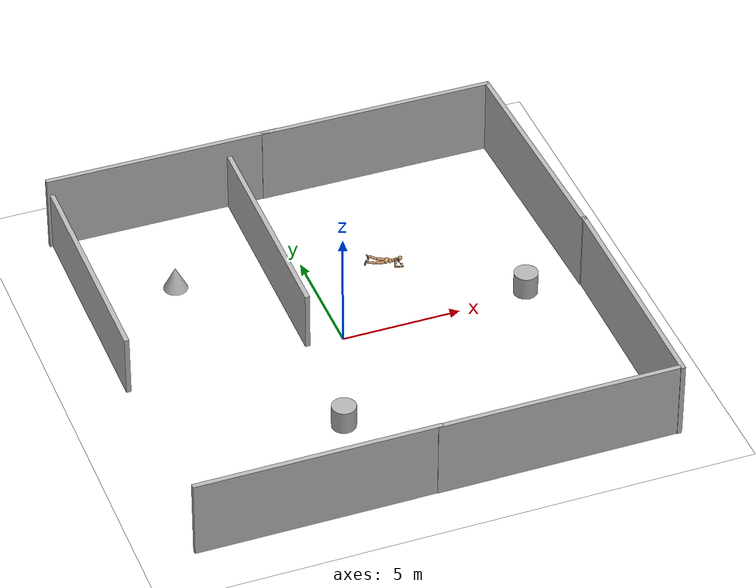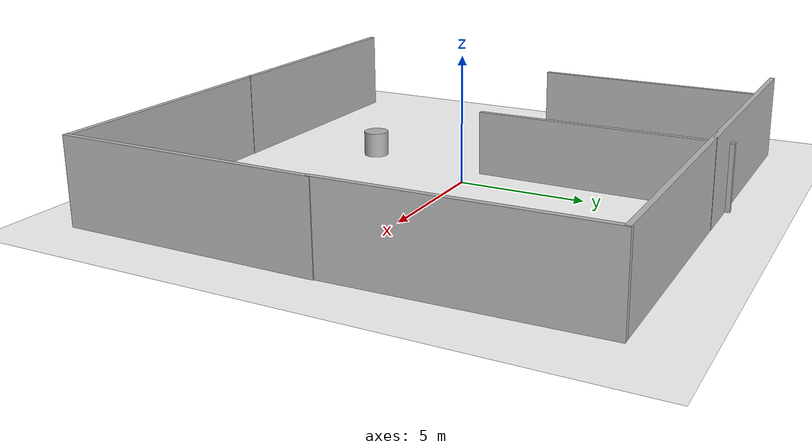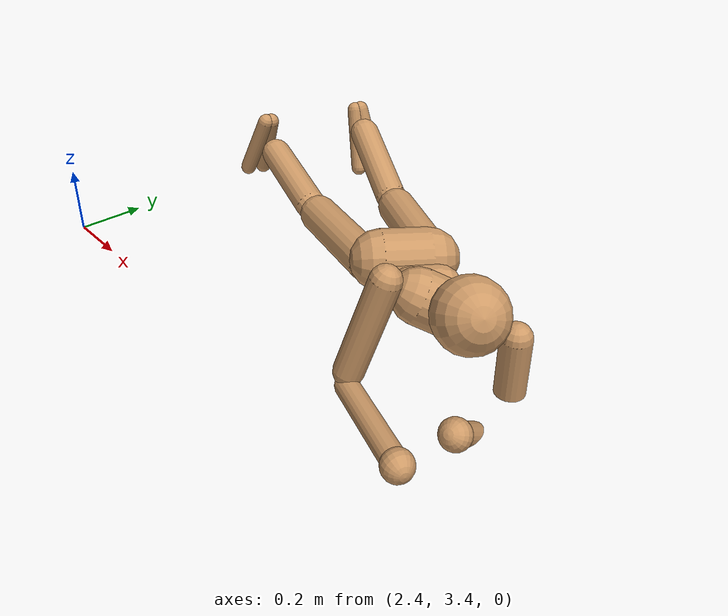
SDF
<sdf version="1.10">
 <world name="empty">
  <physics name="1ms" type="ignored">
   <max_step_size>0.001</max_step_size>
   <real_time_factor>1</real_time_factor>
   <real_time_update_rate>1000</real_time_update_rate>
  </physics>
  <plugin name="gz::sim::systems::Physics" filename="gz-sim-physics-system"/>
  <plugin name="gz::sim::systems::UserCommands" filename="gz-sim-user-commands-system"/>
  <plugin name="gz::sim::systems::SceneBroadcaster" filename="gz-sim-scene-broadcaster-system"/>
  <plugin name="gz::sim::systems::Contact" filename="gz-sim-contact-system"/>
  <plugin name="gz::sim::systems::NavSat" filename="gz-sim-navsat-system"/>
  <spherical_coordinates>
   <surface_model>EARTH_WGS84</surface_model>
   <world_frame_orientation>ENU</world_frame_orientation>
   <latitude_deg>17.723358999999999</latitude_deg>
   <longitude_deg>78.094364999999996</longitude_deg>
   <elevation>0</elevation>
   <heading_deg>0</heading_deg>
  </spherical_coordinates>
  <gravity>0 0 -9.8000000000000007</gravity>
  <magnetic_field>5.5644999999999998e-06 2.2875799999999999e-05 -4.2388400000000002e-05</magnetic_field>
  <atmosphere type="adiabatic"/>
  <scene>
   <ambient>0.400000006 0.400000006 0.400000006 1</ambient>
   <background>0.699999988 0.699999988 0.699999988 1</background>
   <shadows>true</shadows>
  </scene>
  <model name="ground_plane">
   <static>true</static>
   <link name="link">
    <collision name="collision">
     <geometry><plane><normal>0 0 1</normal><size>100 100</size></plane></geometry>
    </collision>
    <visual name="visual">
     <geometry><plane><normal>0 0 1</normal><size>20 20</size></plane></geometry>
     <material>
      <ambient>1 1 1 1</ambient>
      <diffuse>1 1 1 1</diffuse>
      <pbr>
       <metal>
        <albedo_map>file:///home/kiranchand/Downloads/project_2026/grass.jpg</albedo_map>
        <roughness>0.9</roughness>
        <metalness>0.0</metalness>
       </metal>
      </pbr>
     </material>
    </visual>
    <inertial>
     <mass>1</mass>
     <inertia><ixx>1</ixx><ixy>0</ixy><ixz>0</ixz><iyy>1</iyy><iyz>0</iyz><izz>1</izz></inertia>
    </inertial>
   </link>
  </model>
  <model name="cutout_wall">
   <static>true</static>
   <link name="link">
    <pose>0 0 1.3999999999999999 0 0 0</pose>
    <collision name="collision">
     <geometry><box><size>10 0.20000000000000001 3.7999999999999998</size></box></geometry>
     <surface>
      <contact>
       <collide_without_contact>true</collide_without_contact>
       <collide_without_contact_bitmask>2</collide_without_contact_bitmask>
      </contact>
     </surface>
    </collision>
    <visual name="visual">
     <cast_shadows>false</cast_shadows>
     <geometry><box><size>10 0.20000000000000001 3.7999999999999998</size></box></geometry>
     <material>
      <script>
       <uri>https://fuel.gazebosim.org/1.0/openrobotics/models/cutout wall/2/files/materials/scripts</uri>
       <uri>https://fuel.gazebosim.org/1.0/openrobotics/models/cutout wall/2/files/materials/textures</uri>
       <name>drc_practice/cutout_wall</name>
      </script>
     </material>
    </visual>
    <sensor name="mud_contact" type="contact">
     <always_on>true</always_on>
     <update_rate>1000</update_rate>
     <contact><collision>collision</collision><topic>__default_topic__</topic></contact>
    </sensor>
    <inertial>
     <mass>1</mass>
     <inertia><ixx>1</ixx><ixy>0</ixy><ixz>0</ixz><iyy>1</iyy><iyz>0</iyz><izz>1</izz></inertia>
    </inertial>
   </link>
   <plugin name="gazebo_mud" filename="libMudPlugin.so">
    <contact_sensor_name>link/mud_contact</contact_sensor_name>
    <stiffness>0.0</stiffness>
    <damping>40.0</damping>
    <contact_surface_bitmask>2</contact_surface_bitmask>
    <link_name>drill::link</link_name>
   </plugin>
   <pose>-4.2005801200866699 9.8115701675415039 0 0 0 0</pose>
  </model>
  <model name="cutout_wall_0">
   <static>true</static>
   <link name="link">
    <pose>0 0 1.3999999999999999 0 0 0</pose>
    <collision name="collision">
     <geometry><box><size>10 0.20000000000000001 3.7999999999999998</size></box></geometry>
     <surface>
      <contact>
       <collide_without_contact>true</collide_without_contact>
       <collide_without_contact_bitmask>2</collide_without_contact_bitmask>
      </contact>
     </surface>
    </collision>
    <visual name="visual">
     <cast_shadows>false</cast_shadows>
     <geometry><box><size>10 0.20000000000000001 3.7999999999999998</size></box></geometry>
     <material>
      <script>
       <uri>https://fuel.gazebosim.org/1.0/openrobotics/models/cutout wall/2/files/materials/scripts</uri>
       <uri>https://fuel.gazebosim.org/1.0/openrobotics/models/cutout wall/2/files/materials/textures</uri>
       <name>drc_practice/cutout_wall</name>
      </script>
     </material>
    </visual>
    <sensor name="mud_contact" type="contact">
     <always_on>true</always_on>
     <update_rate>1000</update_rate>
     <contact><collision>collision</collision><topic>__default_topic__</topic></contact>
    </sensor>
    <inertial>
     <mass>1</mass>
     <inertia><ixx>1</ixx><ixy>0</ixy><ixz>0</ixz><iyy>1</iyy><iyz>0</iyz><izz>1</izz></inertia>
    </inertial>
   </link>
   <plugin name="gazebo_mud" filename="libMudPlugin.so">
    <contact_sensor_name>link/mud_contact</contact_sensor_name>
    <stiffness>0.0</stiffness>
    <damping>40.0</damping>
    <contact_surface_bitmask>2</contact_surface_bitmask>
    <link_name>drill::link</link_name>
   </plugin>
   <pose>-4.5728732016919889 -9.7548819035040673 0 0 0 0</pose>
  </model>
  <model name="cutout_wall_1">
   <static>true</static>
   <link name="link">
    <pose>0 0 1.3999999999999999 0 0 0</pose>
    <collision name="collision">
     <geometry><box><size>10 0.20000000000000001 3.7999999999999998</size></box></geometry>
     <surface>
      <contact>
       <collide_without_contact>true</collide_without_contact>
       <collide_without_contact_bitmask>2</collide_without_contact_bitmask>
      </contact>
     </surface>
    </collision>
    <visual name="visual">
     <cast_shadows>false</cast_shadows>
     <geometry><box><size>10 0.20000000000000001 3.7999999999999998</size></box></geometry>
     <material>
      <script>
       <uri>https://fuel.gazebosim.org/1.0/openrobotics/models/cutout wall/2/files/materials/scripts</uri>
       <uri>https://fuel.gazebosim.org/1.0/openrobotics/models/cutout wall/2/files/materials/textures</uri>
       <name>drc_practice/cutout_wall</name>
      </script>
     </material>
    </visual>
    <sensor name="mud_contact" type="contact">
     <always_on>true</always_on>
     <update_rate>1000</update_rate>
     <contact><collision>collision</collision><topic>__default_topic__</topic></contact>
    </sensor>
    <inertial>
     <mass>1</mass>
     <inertia><ixx>1</ixx><ixy>0</ixy><ixz>0</ixz><iyy>1</iyy><iyz>0</iyz><izz>1</izz></inertia>
    </inertial>
   </link>
   <plugin name="gazebo_mud" filename="libMudPlugin.so">
    <contact_sensor_name>link/mud_contact</contact_sensor_name>
    <stiffness>0.0</stiffness>
    <damping>40.0</damping>
    <contact_surface_bitmask>2</contact_surface_bitmask>
    <link_name>drill::link</link_name>
   </plugin>
   <pose>5.2112197875976562 -9.7711372375488281 0 0 0 0</pose>
  </model>
  <model name="cutout_wall_2">
   <static>true</static>
   <link name="link">
    <pose>0 0 1.3999999999999999 0 0 0</pose>
    <collision name="collision">
     <geometry><box><size>10 0.20000000000000001 3.7999999999999998</size></box></geometry>
     <surface>
      <contact>
       <collide_without_contact>true</collide_without_contact>
       <collide_without_contact_bitmask>2</collide_without_contact_bitmask>
      </contact>
     </surface>
    </collision>
    <visual name="visual">
     <cast_shadows>false</cast_shadows>
     <geometry><box><size>10 0.20000000000000001 3.7999999999999998</size></box></geometry>
     <material>
      <script>
       <uri>https://fuel.gazebosim.org/1.0/openrobotics/models/cutout wall/2/files/materials/scripts</uri>
       <uri>https://fuel.gazebosim.org/1.0/openrobotics/models/cutout wall/2/files/materials/textures</uri>
       <name>drc_practice/cutout_wall</name>
      </script>
     </material>
    </visual>
    <sensor name="mud_contact" type="contact">
     <always_on>true</always_on>
     <update_rate>1000</update_rate>
     <contact><collision>collision</collision><topic>__default_topic__</topic></contact>
    </sensor>
    <inertial>
     <mass>1</mass>
     <inertia><ixx>1</ixx><ixy>0</ixy><ixz>0</ixz><iyy>1</iyy><iyz>0</iyz><izz>1</izz></inertia>
    </inertial>
   </link>
   <plugin name="gazebo_mud" filename="libMudPlugin.so">
    <contact_sensor_name>link/mud_contact</contact_sensor_name>
    <stiffness>0.0</stiffness>
    <damping>40.0</damping>
    <contact_surface_bitmask>2</contact_surface_bitmask>
    <link_name>drill::link</link_name>
   </plugin>
   <pose>5.0395960807800293 9.7994699478149414 0 0 0 0</pose>
  </model>
  <model name="cutout_wall_3">
   <static>true</static>
   <link name="link">
    <pose>0 0 1.3999999999999999 0 0 0</pose>
    <collision name="collision">
     <geometry><box><size>10 0.20000000000000001 3.7999999999999998</size></box></geometry>
     <surface>
      <contact>
       <collide_without_contact>true</collide_without_contact>
       <collide_without_contact_bitmask>2</collide_without_contact_bitmask>
      </contact>
     </surface>
    </collision>
    <visual name="visual">
     <cast_shadows>false</cast_shadows>
     <geometry><box><size>10 0.20000000000000001 3.7999999999999998</size></box></geometry>
     <material>
      <script>
       <uri>https://fuel.gazebosim.org/1.0/openrobotics/models/cutout wall/2/files/materials/scripts</uri>
       <uri>https://fuel.gazebosim.org/1.0/openrobotics/models/cutout wall/2/files/materials/textures</uri>
       <name>drc_practice/cutout_wall</name>
      </script>
     </material>
    </visual>
    <sensor name="mud_contact" type="contact">
     <always_on>true</always_on>
     <update_rate>1000</update_rate>
     <contact><collision>collision</collision><topic>__default_topic__</topic></contact>
    </sensor>
    <inertial>
     <mass>1</mass>
     <inertia><ixx>1</ixx><ixy>0</ixy><ixz>0</ixz><iyy>1</iyy><iyz>0</iyz><izz>1</izz></inertia>
    </inertial>
   </link>
   <plugin name="gazebo_mud" filename="libMudPlugin.so">
    <contact_sensor_name>link/mud_contact</contact_sensor_name>
    <stiffness>0.0</stiffness>
    <damping>40.0</damping>
    <contact_surface_bitmask>2</contact_surface_bitmask>
    <link_name>drill::link</link_name>
   </plugin>
   <pose>10.142600059509277 4.9063401222229004 -2.2204460492503131e-16 0 0 1.5975869278983041</pose>
  </model>
  <model name="cutout_wall_4">
   <static>true</static>
   <link name="link">
    <pose>0 0 1.3999999999999999 0 0 0</pose>
    <collision name="collision">
     <geometry><box><size>10 0.20000000000000001 3.7999999999999998</size></box></geometry>
     <surface>
      <contact>
       <collide_without_contact>true</collide_without_contact>
       <collide_without_contact_bitmask>2</collide_without_contact_bitmask>
      </contact>
     </surface>
    </collision>
    <visual name="visual">
     <cast_shadows>false</cast_shadows>
     <geometry><box><size>10 0.20000000000000001 3.7999999999999998</size></box></geometry>
     <material>
      <script>
       <uri>https://fuel.gazebosim.org/1.0/openrobotics/models/cutout wall/2/files/materials/scripts</uri>
       <uri>https://fuel.gazebosim.org/1.0/openrobotics/models/cutout wall/2/files/materials/textures</uri>
       <name>drc_practice/cutout_wall</name>
      </script>
     </material>
    </visual>
    <sensor name="mud_contact" type="contact">
     <always_on>true</always_on>
     <update_rate>1000</update_rate>
     <contact><collision>collision</collision><topic>__default_topic__</topic></contact>
    </sensor>
    <inertial>
     <mass>1</mass>
     <inertia><ixx>1</ixx><ixy>0</ixy><ixz>0</ixz><iyy>1</iyy><iyz>0</iyz><izz>1</izz></inertia>
    </inertial>
   </link>
   <plugin name="gazebo_mud" filename="libMudPlugin.so">
    <contact_sensor_name>link/mud_contact</contact_sensor_name>
    <stiffness>0.0</stiffness>
    <damping>40.0</damping>
    <contact_surface_bitmask>2</contact_surface_bitmask>
    <link_name>drill::link</link_name>
   </plugin>
   <pose>10.294502258300781 -4.8952364921569824 4.4408920985006262e-16 0 0 1.5676399480184968</pose>
  </model>
  <model name="humanod_from_mjcf">
   <static>false</static>
   <pose>2.5448099758621097 4.3788755101594283 -0.53820748431299448 -0.71282996008800936 0.85456380769252327 -1.3645939909063616</pose>
   <link name="torso">
    <pose>0 0 1.5 0 0 0</pose>
    <inertial>
     <pose>-0.00386404 0 -0.0463685 0 0.08314120000000004 0</pose>
     <mass>5.8538300000000003</mass>
     <inertia>
      <ixx>0.051274199999999999</ixx>
      <ixy>0</ixy>
      <ixz>0</ixz>
      <iyy>0.031966700000000001</iyy>
      <iyz>0</iyz>
      <izz>0.031149300000000001</izz>
     </inertia>
    </inertial>
    <collision name="collision_torso">
     <pose>0 0 0 1.5708 0 0</pose>
     <geometry>
      <capsule><radius>0.070000000000000007</radius><length>0.14000000000000001</length></capsule>
     </geometry>
     <surface>
      <contact><collide_bitmask>255</collide_bitmask></contact>
      <friction><ode><mu>0.69999999999999996</mu></ode></friction>
     </surface>
    </collision>
    <collision name="collision_upper_waist">
     <pose>-0.01 0 -0.12 1.5708 0 0</pose>
     <geometry><capsule><radius>0.059999999999999998</radius><length>0.12</length></capsule></geometry>
     <surface>
      <contact><collide_bitmask>255</collide_bitmask></contact>
      <friction><ode><mu>0.69999999999999996</mu></ode></friction>
     </surface>
    </collision>
    <light name="top" type="spot">
     <pose>0 0 2 0 0 0</pose>
     <cast_shadows>false</cast_shadows>
     <intensity>1</intensity>
     <direction>0 0 -1</direction>
     <diffuse>0.699999988 0.699999988 0.699999988 1</diffuse>
     <specular>0.300000012 0.300000012 0.300000012 1</specular>
     <attenuation><range>10</range><linear>0</linear><constant>1</constant><quadratic>0</quadratic></attenuation>
     <spot><inner_angle>0</inner_angle><outer_angle>1.5708</outer_angle><falloff>2</falloff></spot>
    </light>
    <sensor name="back" type="camera">
     <pose>-3 0 1 7.8504600000000004e-17 7.8504600000000004e-17 -7.8504600000000004e-17</pose>
     <topic>__default__</topic>
     <update_rate>25</update_rate>
     <enable_metrics>false</enable_metrics>
     <camera name="__default__">
      <horizontal_fov>1.0469999999999999</horizontal_fov>
      <image><width>320</width><height>240</height><format>RGB_INT8</format><anti_aliasing>4</anti_aliasing></image>
      <camera_info_topic>__default__</camera_info_topic>
      <triggered>false</triggered>
      <clip><near>0.10000000000000001</near><far>100</far></clip>
      <save enabled="false"><path>__default__</path></save>
      <visibility_mask>4294967295</visibility_mask>
      <noise><type>none</type><mean>0</mean><stddev>0</stddev></noise>
      <distortion><k1>0</k1><k2>0</k2><k3>0</k3><p1>0</p1><p2>0</p2><center>0.5 0.5</center></distortion>
      <lens>
       <type>stereographic</type>
       <scale_to_hfov>true</scale_to_hfov>
       <cutoff_angle>1.5708</cutoff_angle>
       <env_texture_size>256</env_texture_size>
      </lens>
     </camera>
    </sensor>
    <sensor name="side" type="camera">
     <pose>0 -3 1 2.2204499999999999e-16 2.4651903288156619e-32 1.5708</pose>
     <topic>__default__</topic>
     <update_rate>25</update_rate>
     <enable_metrics>false</enable_metrics>
     <camera name="__default__">
      <horizontal_fov>1.0469999999999999</horizontal_fov>
      <image><width>320</width><height>240</height><format>RGB_INT8</format><anti_aliasing>4</anti_aliasing></image>
      <camera_info_topic>__default__</camera_info_topic>
      <triggered>false</triggered>
      <clip><near>0.10000000000000001</near><far>100</far></clip>
      <save enabled="false"><path>__default__</path></save>
      <visibility_mask>4294967295</visibility_mask>
      <noise><type>none</type><mean>0</mean><stddev>0</stddev></noise>
      <distortion><k1>0</k1><k2>0</k2><k3>0</k3><p1>0</p1><p2>0</p2><center>0.5 0.5</center></distortion>
      <lens>
       <type>stereographic</type>
       <scale_to_hfov>true</scale_to_hfov>
       <cutoff_angle>1.5708</cutoff_angle>
       <env_texture_size>256</env_texture_size>
      </lens>
     </camera>
    </sensor>
    <visual name="visual_torso">
     <pose>0 0 0 1.5708 0 0</pose>
     <geometry>
      <capsule><radius>0.070000000000000007</radius><length>0.14000000000000001</length></capsule>
     </geometry>
     <visibility_flags>4294967295</visibility_flags>
     <material>
      <ambient>0.800000012 0.600000024 0.400000006 1</ambient>
      <diffuse>0.800000012 0.600000024 0.400000006 1</diffuse>
      <specular>0.5 0.5 0.5 1</specular>
      <emissive>0 0 0 1</emissive>
      <render_order>0</render_order>
      <lighting>true</lighting>
      <double_sided>false</double_sided>
      <shader type="pixel"/>
     </material>
    </visual>
    <visual name="visual_upper_waist">
     <pose>-0.01 0 -0.12 1.5708 0 0</pose>
     <geometry><capsule><radius>0.059999999999999998</radius><length>0.12</length></capsule></geometry>
     <visibility_flags>4294967295</visibility_flags>
     <material>
      <ambient>0.800000012 0.600000024 0.400000006 1</ambient>
      <diffuse>0.800000012 0.600000024 0.400000006 1</diffuse>
      <specular>0.5 0.5 0.5 1</specular>
      <emissive>0 0 0 1</emissive>
      <render_order>0</render_order>
      <lighting>true</lighting>
      <double_sided>false</double_sided>
      <shader type="pixel"/>
     </material>
    </visual>
   </link>
   <link name="head">
    <pose>0 1.7763568394002505e-15 1.6900000000000013 1.6653345369377348e-16 -7.1275450819197061e-16 -5.9348734942507915e-32</pose>
    <inertial>
     <mass>3.0536300000000001</mass>
     <inertia>
      <ixx>0.0098937499999999998</ixx>
      <ixy>0</ixy>
      <ixz>0</ixz>
      <iyy>0.0098937499999999998</iyy>
      <iyz>0</iyz>
      <izz>0.0098937499999999998</izz>
     </inertia>
    </inertial>
    <collision name="collision_head">
     <geometry><sphere><radius>0.089999999999999997</radius></sphere></geometry>
     <surface>
      <contact><collide_bitmask>255</collide_bitmask></contact>
      <friction><ode><mu>0.69999999999999996</mu></ode></friction>
     </surface>
    </collision>
    <sensor name="egocentric" type="camera">
     <pose>0.089999999999999997 0 0 2.0641799999999988e-16 0.095166200000000006 -3.2285999999999984e-16</pose>
     <topic>__default__</topic>
     <update_rate>25</update_rate>
     <enable_metrics>false</enable_metrics>
     <camera name="__default__">
      <horizontal_fov>1.0469999999999999</horizontal_fov>
      <image><width>320</width><height>240</height><format>RGB_INT8</format><anti_aliasing>4</anti_aliasing></image>
      <camera_info_topic>__default__</camera_info_topic>
      <triggered>false</triggered>
      <clip><near>0.10000000000000001</near><far>100</far></clip>
      <save enabled="false"><path>__default__</path></save>
      <visibility_mask>4294967295</visibility_mask>
      <noise><type>none</type><mean>0</mean><stddev>0</stddev></noise>
      <distortion><k1>0</k1><k2>0</k2><k3>0</k3><p1>0</p1><p2>0</p2><center>0.5 0.5</center></distortion>
      <lens>
       <type>stereographic</type>
       <scale_to_hfov>true</scale_to_hfov>
       <cutoff_angle>1.5708</cutoff_angle>
       <env_texture_size>256</env_texture_size>
      </lens>
     </camera>
    </sensor>
    <visual name="visual_head">
     <geometry><sphere><radius>0.089999999999999997</radius></sphere></geometry>
     <visibility_flags>4294967295</visibility_flags>
     <material>
      <ambient>0.800000012 0.600000024 0.400000006 1</ambient>
      <diffuse>0.800000012 0.600000024 0.400000006 1</diffuse>
      <specular>0.5 0.5 0.5 1</specular>
      <emissive>0 0 0 1</emissive>
      <render_order>0</render_order>
      <lighting>true</lighting>
      <double_sided>false</double_sided>
      <shader type="pixel"/>
     </material>
    </visual>
   </link>
   <link name="lower_waist">
    <pose>-0.028713365916392508 -0.0093121781888401145 1.2434525120459132 -2.9312527204387672e-17 0.32739137618254172 0.46174321219167797</pose>
    <inertial>
     <pose>0 0 0 1.5708 0 0</pose>
     <mass>2.2619500000000001</mass>
     <inertia>
      <ixx>0.0098530400000000004</ixx>
      <ixy>0</ixy>
      <ixz>0</ixz>
      <iyy>0.0098530400000000004</iyy>
      <iyz>0</iyz>
      <izz>0.0037457800000000002</izz>
     </inertia>
    </inertial>
    <collision name="collision_lower_waist">
     <pose>0 0 0 1.5708 0 0</pose>
     <geometry><capsule><radius>0.059999999999999998</radius><length>0.12</length></capsule></geometry>
     <surface>
      <contact><collide_bitmask>255</collide_bitmask></contact>
      <friction><ode><mu>0.69999999999999996</mu></ode></friction>
     </surface>
    </collision>
    <visual name="visual_lower_waist">
     <pose>0 0 0 1.5708 0 0</pose>
     <geometry><capsule><radius>0.059999999999999998</radius><length>0.12</length></capsule></geometry>
     <visibility_flags>4294967295</visibility_flags>
     <material>
      <ambient>0.800000012 0.600000024 0.400000006 1</ambient>
      <diffuse>0.800000012 0.600000024 0.400000006 1</diffuse>
      <specular>0.5 0.5 0.5 1</specular>
      <emissive>0 0 0 1</emissive>
      <render_order>0</render_order>
      <lighting>true</lighting>
      <double_sided>false</double_sided>
      <shader type="pixel"/>
     </material>
    </visual>
   </link>
   <link name="lower_waist_dummy_0">
    <pose>-0.0099999999999988987 8.8817841970012523e-16 1.2400000000000009 -2.2229199491852151e-16 -9.4567010196203731e-16 0.46174321219167835</pose>
    <inertial>
     <mass>9.9999999999999995e-07</mass>
     <inertia>
      <ixx>3.9999999999999998e-07</ixx>
      <ixy>0</ixy>
      <ixz>0</ixz>
      <iyy>3.9999999999999998e-07</iyy>
      <iyz>0</iyz>
      <izz>3.9999999999999998e-07</izz>
     </inertia>
    </inertial>
   </link>
   <link name="pelvis">
    <pose>-0.077874604998719121 -0.029567527596033649 1.0872838107020317 0.037685347690583022 0.32739137618254088 0.46174321219167741</pose>
    <inertial>
     <pose>-0.02 0 0 1.5708 0 0</pose>
     <mass>6.6161899999999996</mass>
     <inertia>
      <ixx>0.052318000000000003</ixx>
      <ixy>0</ixy>
      <ixz>0</ixz>
      <iyy>0.052318000000000003</iyy>
      <iyz>0</iyz>
      <izz>0.024322099999999999</izz>
     </inertia>
    </inertial>
    <collision name="collision_butt">
     <pose>-0.02 0 0 1.5708 0 0</pose>
     <geometry>
      <capsule><radius>0.089999999999999997</radius><length>0.14000000000000001</length></capsule>
     </geometry>
     <surface>
      <contact><collide_bitmask>255</collide_bitmask></contact>
      <friction><ode><mu>0.69999999999999996</mu></ode></friction>
     </surface>
    </collision>
    <visual name="visual_butt">
     <pose>-0.02 0 0 1.5708 0 0</pose>
     <geometry>
      <capsule><radius>0.089999999999999997</radius><length>0.14000000000000001</length></capsule>
     </geometry>
     <visibility_flags>4294967295</visibility_flags>
     <material>
      <ambient>0.800000012 0.600000024 0.400000006 1</ambient>
      <diffuse>0.800000012 0.600000024 0.400000006 1</diffuse>
      <specular>0.5 0.5 0.5 1</specular>
      <emissive>0 0 0 1</emissive>
      <render_order>0</render_order>
      <lighting>true</lighting>
      <double_sided>false</double_sided>
      <shader type="pixel"/>
     </material>
    </visual>
   </link>
   <link name="right_thigh">
    <pose>-0.046619138292701479 -0.12394872332954066 1.0458678030129474 -0.34054518011049906 0.4595290586002167 0.39873370778583783</pose>
    <inertial>
     <pose>0 0.0050000000000000001 -0.17000000000000001 0.02940329999999999 0 0</pose>
     <mass>4.7517500000000004</mass>
     <inertia>
      <ixx>0.074951699999999996</ixx>
      <ixy>0</ixy>
      <ixz>0</ixz>
      <iyy>0.074951699999999996</iyy>
      <iyz>0</iyz>
      <izz>0.0082274300000000009</izz>
     </inertia>
    </inertial>
    <collision name="collision_right_thigh">
     <pose>0 0.0050000000000000001 -0.17000000000000001 0.029403299999999993 0 0</pose>
     <geometry>
      <capsule><radius>0.059999999999999998</radius><length>0.34014699999999998</length></capsule>
     </geometry>
     <surface>
      <contact><collide_bitmask>255</collide_bitmask></contact>
      <friction><ode><mu>0.69999999999999996</mu></ode></friction>
     </surface>
    </collision>
    <visual name="visual_right_thigh">
     <pose>0 0.0050000000000000001 -0.17000000000000001 0.029403299999999993 0 0</pose>
     <geometry>
      <capsule><radius>0.059999999999999998</radius><length>0.34014699999999998</length></capsule>
     </geometry>
     <visibility_flags>4294967295</visibility_flags>
     <material>
      <ambient>0.800000012 0.600000024 0.400000006 1</ambient>
      <diffuse>0.800000012 0.600000024 0.400000006 1</diffuse>
      <specular>0.5 0.5 0.5 1</specular>
      <emissive>0 0 0 1</emissive>
      <render_order>0</render_order>
      <lighting>true</lighting>
      <double_sided>false</double_sided>
      <shader type="pixel"/>
     </material>
    </visual>
   </link>
   <link name="right_thigh_dummy_0">
    <pose>-0.046618132881000029 -0.12394867423652745 1.0458678482773707 -0.31723047312103386 0.32738736892012427 0.46174055459103008</pose>
    <inertial>
     <mass>9.9999999999999995e-07</mass>
     <inertia>
      <ixx>3.9999999999999998e-07</ixx>
      <ixy>0</ixy>
      <ixz>0</ixz>
      <iyy>3.9999999999999998e-07</iyy>
      <iyz>0</iyz>
      <izz>3.9999999999999998e-07</izz>
     </inertia>
    </inertial>
   </link>
   <link name="right_thigh_dummy_1">
    <pose>-0.046618132881000029 -0.12394867423652745 1.0458678482773713 -0.32122774724551906 0.32347174062191397 0.44923814021391423</pose>
    <inertial>
     <mass>9.9999999999999995e-07</mass>
     <inertia>
      <ixx>3.9999999999999998e-07</ixx>
      <ixy>0</ixy>
      <ixz>0</ixz>
      <iyy>3.9999999999999998e-07</iyy>
      <iyz>0</iyz>
      <izz>3.9999999999999998e-07</izz>
     </inertia>
    </inertial>
   </link>
   <link name="right_shin">
    <pose>-0.15851596583142369 -0.30670514780440072 0.70509672438244209 -0.39848238343238479 0.68960230685647683 0.29290224150087368</pose>
    <inertial>
     <pose>0 0 -0.14999999999999999 0 0 0</pose>
     <mass>2.7557</mass>
     <inertia>
      <ixx>0.032607999999999998</ixx>
      <ixy>0</ixy>
      <ixz>0</ixz>
      <iyy>0.032607999999999998</iyy>
      <iyz>0</iyz>
      <izz>0.0031898899999999999</izz>
     </inertia>
    </inertial>
    <collision name="collision_right_shin">
     <pose>0 0 -0.14999999999999999 0 0 0</pose>
     <geometry>
      <capsule><radius>0.049000000000000002</radius><length>0.29999999999999999</length></capsule>
     </geometry>
     <surface>
      <contact><collide_bitmask>255</collide_bitmask></contact>
      <friction><ode><mu>0.69999999999999996</mu></ode></friction>
     </surface>
    </collision>
    <visual name="visual_right_shin">
     <pose>0 0 -0.14999999999999999 0 0 0</pose>
     <geometry>
      <capsule><radius>0.049000000000000002</radius><length>0.29999999999999999</length></capsule>
     </geometry>
     <visibility_flags>4294967295</visibility_flags>
     <material>
      <ambient>0.800000012 0.600000024 0.400000006 1</ambient>
      <diffuse>0.800000012 0.600000024 0.400000006 1</diffuse>
      <specular>0.5 0.5 0.5 1</specular>
      <emissive>0 0 0 1</emissive>
      <render_order>0</render_order>
      <lighting>true</lighting>
      <double_sided>false</double_sided>
      <shader type="pixel"/>
     </material>
    </visual>
   </link>
   <link name="right_foot">
    <pose>-0.34024670426983494 -0.52168910949273695 0.43616303184288063 -0.54512351942040893 0.79993000925645397 0.17445295693411811</pose>
    <inertial>
     <pose>0.035000000000000003 -0.01 0 2.6535897933102466e-06 -1.5707926536359933 3.1415926535897931</pose>
     <mass>1.13114</mass>
     <inertia>
      <ixx>0.0064464600000000002</ixx>
      <ixy>0</ixy>
      <ixz>0</ixz>
      <iyy>0.0059437200000000004</iyy>
      <iyz>0</iyz>
      <izz>0.00090301699999999999</izz>
     </inertia>
    </inertial>
    <collision name="collision_right_right_foot">
     <pose>0.035000000000000003 -0.029999999999999999 0 -1.5707999999999998 -1.47584 1.47584</pose>
     <geometry><capsule><radius>0.027</radius><length>0.21095</length></capsule></geometry>
     <surface>
      <contact><collide_bitmask>255</collide_bitmask></contact>
      <friction><ode><mu>0.69999999999999996</mu></ode></friction>
     </surface>
    </collision>
    <collision name="collision_left_right_foot">
     <pose>0.035000000000000003 0.01 0 1.5707999999999998 -1.47584 -1.47584</pose>
     <geometry><capsule><radius>0.027</radius><length>0.21095</length></capsule></geometry>
     <surface>
      <contact><collide_bitmask>255</collide_bitmask></contact>
      <friction><ode><mu>0.69999999999999996</mu></ode></friction>
     </surface>
    </collision>
    <visual name="visual_right_right_foot">
     <pose>0.035000000000000003 -0.029999999999999999 0 -1.5707999999999998 -1.47584 1.47584</pose>
     <geometry><capsule><radius>0.027</radius><length>0.21095</length></capsule></geometry>
     <visibility_flags>4294967295</visibility_flags>
     <material>
      <ambient>0.800000012 0.600000024 0.400000006 1</ambient>
      <diffuse>0.800000012 0.600000024 0.400000006 1</diffuse>
      <specular>0.5 0.5 0.5 1</specular>
      <emissive>0 0 0 1</emissive>
      <render_order>0</render_order>
      <lighting>true</lighting>
      <double_sided>false</double_sided>
      <shader type="pixel"/>
     </material>
    </visual>
    <visual name="visual_left_right_foot">
     <pose>0.035000000000000003 0.01 0 1.5707999999999998 -1.47584 -1.47584</pose>
     <geometry><capsule><radius>0.027</radius><length>0.21095</length></capsule></geometry>
     <visibility_flags>4294967295</visibility_flags>
     <material>
      <ambient>0.800000012 0.600000024 0.400000006 1</ambient>
      <diffuse>0.800000012 0.600000024 0.400000006 1</diffuse>
      <specular>0.5 0.5 0.5 1</specular>
      <emissive>0 0 0 1</emissive>
      <render_order>0</render_order>
      <lighting>true</lighting>
      <double_sided>false</double_sided>
      <shader type="pixel"/>
     </material>
    </visual>
   </link>
   <link name="right_foot_dummy_0">
    <pose>-0.34154866673836626 -0.51965567545195412 0.4353174233925754 -0.45177926445464667 0.81522141683491112 0.21508922472239589</pose>
    <inertial>
     <mass>9.9999999999999995e-07</mass>
     <inertia>
      <ixx>3.9999999999999998e-07</ixx>
      <ixy>0</ixy>
      <ixz>0</ixz>
      <iyy>3.9999999999999998e-07</iyy>
      <iyz>0</iyz>
      <izz>3.9999999999999998e-07</izz>
     </inertia>
    </inertial>
   </link>
   <link name="left_thigh">
    <pose>-0.13348718239118629 0.056059301212010304 1.0530020624678933 0.01259513654903311 0.52148337464991723 0.65292000145459606</pose>
    <inertial>
     <pose>0 -0.0050000000000000001 -0.17000000000000001 -0.02940329999999999 0 0</pose>
     <mass>4.7517500000000004</mass>
     <inertia>
      <ixx>0.074951699999999996</ixx>
      <ixy>0</ixy>
      <ixz>0</ixz>
      <iyy>0.074951699999999996</iyy>
      <iyz>0</iyz>
      <izz>0.0082274300000000009</izz>
     </inertia>
    </inertial>
    <collision name="collision_left_thigh">
     <pose>0 -0.0050000000000000001 -0.17000000000000001 -0.029403299999999993 0 0</pose>
     <geometry>
      <capsule><radius>0.059999999999999998</radius><length>0.34014699999999998</length></capsule>
     </geometry>
     <surface>
      <contact><collide_bitmask>255</collide_bitmask></contact>
      <friction><ode><mu>0.69999999999999996</mu></ode></friction>
     </surface>
    </collision>
    <visual name="visual_left_thigh">
     <pose>0 -0.0050000000000000001 -0.17000000000000001 -0.029403299999999993 0 0</pose>
     <geometry>
      <capsule><radius>0.059999999999999998</radius><length>0.34014699999999998</length></capsule>
     </geometry>
     <visibility_flags>4294967295</visibility_flags>
     <material>
      <ambient>0.800000012 0.600000024 0.400000006 1</ambient>
      <diffuse>0.800000012 0.600000024 0.400000006 1</diffuse>
      <specular>0.5 0.5 0.5 1</specular>
      <emissive>0 0 0 1</emissive>
      <render_order>0</render_order>
      <lighting>true</lighting>
      <double_sided>false</double_sided>
      <shader type="pixel"/>
     </material>
    </visual>
   </link>
   <link name="left_thigh_dummy_0">
    <pose>-0.13348718239118718 0.056059301212009416 1.0530020624678937 -0.049585592036656197 0.32738736892012432 0.46174055459103003</pose>
    <inertial>
     <mass>9.9999999999999995e-07</mass>
     <inertia>
      <ixx>3.9999999999999998e-07</ixx>
      <ixy>0</ixy>
      <ixz>0</ixz>
      <iyy>3.9999999999999998e-07</iyy>
      <iyz>0</iyz>
      <izz>3.9999999999999998e-07</izz>
     </inertia>
    </inertial>
   </link>
   <link name="left_thigh_dummy_1">
    <pose>-0.13348718239118629 0.056059301212010304 1.0530020624678933 0.011546979827897328 0.33079343120468235 0.6503958055989697</pose>
    <inertial>
     <mass>9.9999999999999995e-07</mass>
     <inertia>
      <ixx>3.9999999999999998e-07</ixx>
      <ixy>0</ixy>
      <ixz>0</ixz>
      <iyy>3.9999999999999998e-07</iyy>
      <iyz>0</iyz>
      <izz>3.9999999999999998e-07</izz>
     </inertia>
    </inertial>
   </link>
   <link name="left_shin">
    <pose>-0.29466980349246574 -0.073439466434549239 0.70863910885454062 0.01791852227785835 0.91536924943852105 0.66085142078668613</pose>
    <inertial>
     <pose>0 0 -0.14999999999999999 0 0 0</pose>
     <mass>2.7557</mass>
     <inertia>
      <ixx>0.032607999999999998</ixx>
      <ixy>0</ixy>
      <ixz>0</ixz>
      <iyy>0.032607999999999998</iyy>
      <iyz>0</iyz>
      <izz>0.0031898899999999999</izz>
     </inertia>
    </inertial>
    <collision name="collision_left_shin">
     <pose>0 0 -0.14999999999999999 0 0 0</pose>
     <geometry>
      <capsule><radius>0.049000000000000002</radius><length>0.29999999999999999</length></capsule>
     </geometry>
     <surface>
      <contact><collide_bitmask>255</collide_bitmask></contact>
      <friction><ode><mu>0.69999999999999996</mu></ode></friction>
     </surface>
    </collision>
    <visual name="visual_left_shin">
     <pose>0 0 -0.14999999999999999 0 0 0</pose>
     <geometry>
      <capsule><radius>0.049000000000000002</radius><length>0.29999999999999999</length></capsule>
     </geometry>
     <visibility_flags>4294967295</visibility_flags>
     <material>
      <ambient>0.800000012 0.600000024 0.400000006 1</ambient>
      <diffuse>0.800000012 0.600000024 0.400000006 1</diffuse>
      <specular>0.5 0.5 0.5 1</specular>
      <emissive>0 0 0 1</emissive>
      <render_order>0</render_order>
      <lighting>true</lighting>
      <double_sided>false</double_sided>
      <shader type="pixel"/>
     </material>
    </visual>
   </link>
   <link name="left_foot">
    <pose>-0.50506601759411174 -0.23138492137201361 0.44166201898431989 -0.050130662716247471 0.21726621521710293 0.62079886786259719</pose>
    <inertial>
     <pose>0.035000000000000003 0.01 0 2.6535897933102466e-06 -1.5707926536359933 3.1415926535897931</pose>
     <mass>1.13114</mass>
     <inertia>
      <ixx>0.0064464600000000002</ixx>
      <ixy>0</ixy>
      <ixz>0</ixz>
      <iyy>0.0059437200000000004</iyy>
      <iyz>0</iyz>
      <izz>0.00090301699999999999</izz>
     </inertia>
    </inertial>
    <collision name="collision_left_left_foot">
     <pose>0.035000000000000003 0.029999999999999999 0 1.5707999999999998 -1.47584 -1.47584</pose>
     <geometry><capsule><radius>0.027</radius><length>0.21095</length></capsule></geometry>
     <surface>
      <contact><collide_bitmask>255</collide_bitmask></contact>
      <friction><ode><mu>0.69999999999999996</mu></ode></friction>
     </surface>
    </collision>
    <collision name="collision_right_left_foot">
     <pose>0.035000000000000003 -0.01 0 -1.5707999999999998 -1.47584 1.47584</pose>
     <geometry><capsule><radius>0.027</radius><length>0.21095</length></capsule></geometry>
     <surface>
      <contact><collide_bitmask>255</collide_bitmask></contact>
      <friction><ode><mu>0.69999999999999996</mu></ode></friction>
     </surface>
    </collision>
    <visual name="visual_left_left_foot">
     <pose>0.035000000000000003 0.029999999999999999 0 1.5707999999999998 -1.47584 -1.47584</pose>
     <geometry><capsule><radius>0.027</radius><length>0.21095</length></capsule></geometry>
     <visibility_flags>4294967295</visibility_flags>
     <material>
      <ambient>0.800000012 0.600000024 0.400000006 1</ambient>
      <diffuse>0.800000012 0.600000024 0.400000006 1</diffuse>
      <specular>0.5 0.5 0.5 1</specular>
      <emissive>0 0 0 1</emissive>
      <render_order>0</render_order>
      <lighting>true</lighting>
      <double_sided>false</double_sided>
      <shader type="pixel"/>
     </material>
    </visual>
    <visual name="visual_right_left_foot">
     <pose>0.035000000000000003 -0.01 0 -1.5707999999999998 -1.47584 1.47584</pose>
     <geometry><capsule><radius>0.027</radius><length>0.21095</length></capsule></geometry>
     <visibility_flags>4294967295</visibility_flags>
     <material>
      <ambient>0.800000012 0.600000024 0.400000006 1</ambient>
      <diffuse>0.800000012 0.600000024 0.400000006 1</diffuse>
      <specular>0.5 0.5 0.5 1</specular>
      <emissive>0 0 0 1</emissive>
      <render_order>0</render_order>
      <lighting>true</lighting>
      <double_sided>false</double_sided>
      <shader type="pixel"/>
     </material>
    </visual>
   </link>
   <link name="left_foot_dummy_0">
    <pose>-0.50638293090790931 -0.22961296716690249 0.44162003246023707 0.011185201874225824 0.21780371492461803 0.64906233079317732</pose>
    <inertial>
     <mass>9.9999999999999995e-07</mass>
     <inertia>
      <ixx>3.9999999999999998e-07</ixx>
      <ixy>0</ixy>
      <ixz>0</ixz>
      <iyy>3.9999999999999998e-07</iyy>
      <iyz>0</iyz>
      <izz>3.9999999999999998e-07</izz>
     </inertia>
    </inertial>
   </link>
   <link name="right_upper_arm">
    <pose>-4.4408920985006262e-16 -0.16999999999999993 1.5599999999999992 0.48884114961825337 -0.3551265585519926 0.44174148382715939</pose>
    <inertial>
     <pose>0.080000000000000002 -0.080000000000000002 -0.080000000000000002 -0.78539800000000026 -0.61548000000000003 0.26179900000000006</pose>
     <mass>1.6610799999999999</mass>
     <inertia>
      <ixx>0.015905499999999999</ixx>
      <ixy>0</ixy>
      <ixz>0</ixz>
      <iyy>0.015905499999999999</iyy>
      <iyz>0</iyz>
      <izz>0.00128597</izz>
     </inertia>
    </inertial>
    <collision name="collision_right_upper_arm">
     <pose>0.080000000000000002 -0.080000000000000002 -0.080000000000000002 -0.78539800000000026 -0.61548000000000003 0.26179900000000006</pose>
     <geometry>
      <capsule><radius>0.040000000000000001</radius><length>0.27712799999999999</length></capsule>
     </geometry>
     <surface>
      <contact><collide_bitmask>255</collide_bitmask></contact>
      <friction><ode><mu>0.69999999999999996</mu></ode></friction>
     </surface>
    </collision>
    <visual name="visual_right_upper_arm">
     <pose>0.080000000000000002 -0.080000000000000002 -0.080000000000000002 -0.78539800000000026 -0.61548000000000003 0.26179900000000006</pose>
     <geometry>
      <capsule><radius>0.040000000000000001</radius><length>0.27712799999999999</length></capsule>
     </geometry>
     <visibility_flags>4294967295</visibility_flags>
     <material>
      <ambient>0.800000012 0.600000024 0.400000006 1</ambient>
      <diffuse>0.800000012 0.600000024 0.400000006 1</diffuse>
      <specular>0.5 0.5 0.5 1</specular>
      <emissive>0 0 0 1</emissive>
      <render_order>0</render_order>
      <lighting>true</lighting>
      <double_sided>false</double_sided>
      <shader type="pixel"/>
     </material>
    </visual>
   </link>
   <link name="right_upper_arm_dummy_0">
    <pose>-4.4408920985006262e-16 -0.16999999999999904 1.5600000000000001 0.50367271725719054 0.17023334289219172 0.28689726820990608</pose>
    <inertial>
     <mass>9.9999999999999995e-07</mass>
     <inertia>
      <ixx>3.9999999999999998e-07</ixx>
      <ixy>0</ixy>
      <ixz>0</ixz>
      <iyy>3.9999999999999998e-07</iyy>
      <iyz>0</iyz>
      <izz>3.9999999999999998e-07</izz>
     </inertia>
    </inertial>
   </link>
   <link name="right_lower_arm">
    <pose>0.26089368501057897 -0.12890924585350039 1.3943315508454539 0.50249954607003289 -0.19230044120325504 0.39138979437184923</pose>
    <inertial>
     <pose>0.089999999999999997 0.089999999999999997 0.089999999999999997 2.3561899999999998 -0.61548000000000003 -1.3089999999999999</pose>
     <mass>0.96145800000000003</mass>
     <inertia>
      <ixx>0.0084016200000000003</ixx>
      <ixy>0</ixy>
      <ixz>0</ixz>
      <iyy>0.0084016200000000003</iyy>
      <iyz>0</iyz>
      <izz>0.00044998800000000002</izz>
     </inertia>
    </inertial>
    <collision name="collision_right_lower_arm">
     <pose>0.089999999999999997 0.089999999999999997 0.089999999999999997 2.3561899999999998 -0.61548000000000003 -1.3089999999999999</pose>
     <geometry><capsule><radius>0.031</radius><length>0.27712799999999999</length></capsule></geometry>
     <surface>
      <contact><collide_bitmask>255</collide_bitmask></contact>
      <friction><ode><mu>0.69999999999999996</mu></ode></friction>
     </surface>
    </collision>
    <visual name="visual_right_lower_arm">
     <pose>0.089999999999999997 0.089999999999999997 0.089999999999999997 2.3561899999999998 -0.61548000000000003 -1.3089999999999999</pose>
     <geometry><capsule><radius>0.031</radius><length>0.27712799999999999</length></capsule></geometry>
     <visibility_flags>4294967295</visibility_flags>
     <material>
      <ambient>0.800000012 0.600000024 0.400000006 1</ambient>
      <diffuse>0.800000012 0.600000024 0.400000006 1</diffuse>
      <specular>0.5 0.5 0.5 1</specular>
      <emissive>0 0 0 1</emissive>
      <render_order>0</render_order>
      <lighting>true</lighting>
      <double_sided>false</double_sided>
      <shader type="pixel"/>
     </material>
    </visual>
   </link>
   <link name="right_hand">
    <pose>0.35392450165831857 -0.01364678599509439 1.6686668065113004 0.50249954607003444 -0.19230044120325437 0.39138979437184773</pose>
    <inertial>
     <pose>0 0 0 -0.78539800000000026 0.61548000000000003 -0.26179900000000006</pose>
     <mass>0.26808300000000002</mass>
     <inertia>
      <ixx>0.00017157300000000001</ixx>
      <ixy>0</ixy>
      <ixz>0</ixz>
      <iyy>0.00017157300000000001</iyy>
      <iyz>0</iyz>
      <izz>0.00017157300000000001</izz>
     </inertia>
    </inertial>
    <collision name="collision_right_hand">
     <pose>0 0 0 -0.78539800000000026 0.61548000000000003 -0.26179900000000006</pose>
     <geometry><sphere><radius>0.040000000000000001</radius></sphere></geometry>
     <surface>
      <contact><collide_bitmask>255</collide_bitmask></contact>
      <friction><ode><mu>0.69999999999999996</mu></ode></friction>
     </surface>
    </collision>
    <visual name="visual_right_hand">
     <pose>0 0 0 -0.78539800000000026 0.61548000000000003 -0.26179900000000006</pose>
     <geometry><sphere><radius>0.040000000000000001</radius></sphere></geometry>
     <visibility_flags>4294967295</visibility_flags>
     <material>
      <ambient>0.800000012 0.600000024 0.400000006 1</ambient>
      <diffuse>0.800000012 0.600000024 0.400000006 1</diffuse>
      <specular>0.5 0.5 0.5 1</specular>
      <emissive>0 0 0 1</emissive>
      <render_order>0</render_order>
      <lighting>true</lighting>
      <double_sided>false</double_sided>
      <shader type="pixel"/>
     </material>
    </visual>
   </link>
   <link name="left_upper_arm">
    <pose>-4.4408920985006262e-16 0.17000000000000082 1.5600000000000005 -0.04488350867732141 -0.13767244240623258 -0.17500653261690008</pose>
    <inertial>
     <pose>0.080000000000000002 0.080000000000000002 -0.080000000000000002 0.78539800000000026 -0.61548000000000003 -0.26179900000000006</pose>
     <mass>1.6610799999999999</mass>
     <inertia>
      <ixx>0.015905499999999999</ixx>
      <ixy>0</ixy>
      <ixz>0</ixz>
      <iyy>0.015905499999999999</iyy>
      <iyz>0</iyz>
      <izz>0.00128597</izz>
     </inertia>
    </inertial>
    <collision name="collision_left_upper_arm">
     <pose>0.080000000000000002 0.080000000000000002 -0.080000000000000002 0.78539800000000026 -0.61548000000000003 -0.26179900000000006</pose>
     <geometry>
      <capsule><radius>0.040000000000000001</radius><length>0.27712799999999999</length></capsule>
     </geometry>
     <surface>
      <contact><collide_bitmask>255</collide_bitmask></contact>
      <friction><ode><mu>0.69999999999999996</mu></ode></friction>
     </surface>
    </collision>
    <visual name="visual_left_upper_arm">
     <pose>0.080000000000000002 0.080000000000000002 -0.080000000000000002 0.78539800000000026 -0.61548000000000003 -0.26179900000000006</pose>
     <geometry>
      <capsule><radius>0.040000000000000001</radius><length>0.27712799999999999</length></capsule>
     </geometry>
     <visibility_flags>4294967295</visibility_flags>
     <material>
      <ambient>0.800000012 0.600000024 0.400000006 1</ambient>
      <diffuse>0.800000012 0.600000024 0.400000006 1</diffuse>
      <specular>0.5 0.5 0.5 1</specular>
      <emissive>0 0 0 1</emissive>
      <render_order>0</render_order>
      <lighting>true</lighting>
      <double_sided>false</double_sided>
      <shader type="pixel"/>
     </material>
    </visual>
   </link>
   <link name="left_upper_arm_dummy_0">
    <pose>-8.8817841970012523e-16 0.17000000000000082 1.5600000000000016 -0.053201169414376345 0.025709624756734092 -0.027114957766811242</pose>
    <inertial>
     <mass>9.9999999999999995e-07</mass>
     <inertia>
      <ixx>3.9999999999999998e-07</ixx>
      <ixy>0</ixy>
      <ixz>0</ixz>
      <iyy>3.9999999999999998e-07</iyy>
      <iyz>0</iyz>
      <izz>3.9999999999999998e-07</izz>
     </inertia>
    </inertial>
   </link>
   <link name="left_lower_arm">
    <pose>0.23086875664604722 0.30358525020578497 1.3985856322003341 0.015905002022641234 -0.37524824613563434 -0.4119238845004583</pose>
    <inertial>
     <pose>0.089999999999999997 -0.089999999999999997 0.089999999999999997 -2.3561899999999998 -0.61548000000000003 1.3089999999999999</pose>
     <mass>0.96145800000000003</mass>
     <inertia>
      <ixx>0.0084016200000000003</ixx>
      <ixy>0</ixy>
      <ixz>0</ixz>
      <iyy>0.0084016200000000003</iyy>
      <iyz>0</iyz>
      <izz>0.00044998800000000002</izz>
     </inertia>
    </inertial>
    <collision name="collision_left_lower_arm">
     <pose>0.089999999999999997 -0.089999999999999997 0.089999999999999997 -2.3561899999999998 -0.61548000000000003 1.3089999999999999</pose>
     <geometry><capsule><radius>0.031</radius><length>0.27712799999999999</length></capsule></geometry>
     <surface>
      <contact><collide_bitmask>255</collide_bitmask></contact>
      <friction><ode><mu>0.69999999999999996</mu></ode></friction>
     </surface>
    </collision>
    <visual name="visual_left_lower_arm">
     <pose>0.089999999999999997 -0.089999999999999997 0.089999999999999997 -2.3561899999999998 -0.61548000000000003 1.3089999999999999</pose>
     <geometry><capsule><radius>0.031</radius><length>0.27712799999999999</length></capsule></geometry>
     <visibility_flags>4294967295</visibility_flags>
     <material>
      <ambient>0.800000012 0.600000024 0.400000006 1</ambient>
      <diffuse>0.800000012 0.600000024 0.400000006 1</diffuse>
      <specular>0.5 0.5 0.5 1</specular>
      <emissive>0 0 0 1</emissive>
      <render_order>0</render_order>
      <lighting>true</lighting>
      <double_sided>false</double_sided>
      <shader type="pixel"/>
     </material>
    </visual>
   </link>
   <link name="left_hand">
    <pose>0.25164740358456861 0.094976363058451696 1.6293465041751038 0.015905002022642209 -0.37524824613563518 -0.4119238845004598</pose>
    <inertial>
     <pose>0 0 0 0.78539800000000026 0.61548000000000003 0.26179900000000006</pose>
     <mass>0.26808300000000002</mass>
     <inertia>
      <ixx>0.00017157300000000001</ixx>
      <ixy>0</ixy>
      <ixz>0</ixz>
      <iyy>0.00017157300000000001</iyy>
      <iyz>0</iyz>
      <izz>0.00017157300000000001</izz>
     </inertia>
    </inertial>
    <collision name="collision_left_hand">
     <pose>0 0 0 0.78539800000000026 0.61548000000000003 0.26179900000000006</pose>
     <geometry><sphere><radius>0.040000000000000001</radius></sphere></geometry>
     <surface>
      <contact><collide_bitmask>255</collide_bitmask></contact>
      <friction><ode><mu>0.69999999999999996</mu></ode></friction>
     </surface>
    </collision>
    <visual name="visual_left_hand">
     <pose>0 0 0 0.78539800000000026 0.61548000000000003 0.26179900000000006</pose>
     <geometry><sphere><radius>0.040000000000000001</radius></sphere></geometry>
     <visibility_flags>4294967295</visibility_flags>
     <material>
      <ambient>0.800000012 0.600000024 0.400000006 1</ambient>
      <diffuse>0.800000012 0.600000024 0.400000006 1</diffuse>
      <specular>0.5 0.5 0.5 1</specular>
      <emissive>0 0 0 1</emissive>
      <render_order>0</render_order>
      <lighting>true</lighting>
      <double_sided>false</double_sided>
      <shader type="pixel"/>
     </material>
    </visual>
   </link>
   <joint name="fixed_torso_head_joint" type="fixed"><parent>torso</parent><child>head</child></joint>
   <joint name="joint_abdomen_z" type="revolute">
    <pose>0 0 0.064999999999999947 0 0 0</pose>
    <parent>torso</parent>
    <child>lower_waist_dummy_0</child>
    <axis>
     <xyz>0 0 1</xyz>
     <limit>
      <lower>-0.78539800000000004</lower>
      <upper>0.78539800000000004</upper>
      <effort>inf</effort>
      <velocity>inf</velocity>
      <stiffness>100000000</stiffness>
      <dissipation>1</dissipation>
     </limit>
     <dynamics>
      <spring_reference>0</spring_reference>
      <spring_stiffness>20</spring_stiffness>
      <damping>5</damping>
      <friction>0</friction>
     </dynamics>
    </axis>
   </joint>
   <joint name="joint_abdomen_y" type="revolute">
    <pose>0 0 0.064999999999999947 0 0 0</pose>
    <parent>lower_waist_dummy_0</parent>
    <child>lower_waist</child>
    <axis>
     <xyz>0 1 0</xyz>
     <limit>
      <lower>-1.3089999999999999</lower>
      <upper>0.52359900000000004</upper>
      <effort>inf</effort>
      <velocity>inf</velocity>
      <stiffness>100000000</stiffness>
      <dissipation>1</dissipation>
     </limit>
     <dynamics>
      <spring_reference>0</spring_reference>
      <spring_stiffness>10</spring_stiffness>
      <damping>5</damping>
      <friction>0</friction>
     </dynamics>
    </axis>
   </joint>
   <joint name="joint_abdomen_x" type="revolute">
    <pose>0 0 0.10000000000000009 0 0 0</pose>
    <parent>lower_waist</parent>
    <child>pelvis</child>
    <axis>
     <xyz>1 0 0</xyz>
     <limit>
      <lower>-0.61086499999999999</lower>
      <upper>0.61086499999999999</upper>
      <effort>inf</effort>
      <velocity>inf</velocity>
      <stiffness>100000000</stiffness>
      <dissipation>1</dissipation>
     </limit>
     <dynamics>
      <spring_reference>0</spring_reference>
      <spring_stiffness>10</spring_stiffness>
      <damping>5</damping>
      <friction>0</friction>
     </dynamics>
    </axis>
   </joint>
   <joint name="joint_right_hip_x" type="revolute">
    <parent>pelvis</parent>
    <child>right_thigh_dummy_0</child>
    <axis>
     <xyz>1 0 0</xyz>
     <limit>
      <lower>-0.436332</lower>
      <upper>0.087266499999999997</upper>
      <effort>inf</effort>
      <velocity>inf</velocity>
      <stiffness>100000000</stiffness>
      <dissipation>1</dissipation>
     </limit>
     <dynamics>
      <spring_reference>0</spring_reference>
      <spring_stiffness>10</spring_stiffness>
      <damping>5</damping>
      <friction>0</friction>
     </dynamics>
    </axis>
   </joint>
   <joint name="joint_right_hip_z" type="revolute">
    <parent>right_thigh_dummy_0</parent>
    <child>right_thigh_dummy_1</child>
    <axis>
     <xyz>0 0 1</xyz>
     <limit>
      <lower>-1.0471999999999999</lower>
      <upper>0.61086499999999999</upper>
      <effort>inf</effort>
      <velocity>inf</velocity>
      <stiffness>100000000</stiffness>
      <dissipation>1</dissipation>
     </limit>
     <dynamics>
      <spring_reference>0</spring_reference>
      <spring_stiffness>10</spring_stiffness>
      <damping>5</damping>
      <friction>0</friction>
     </dynamics>
    </axis>
   </joint>
   <joint name="joint_right_hip_y" type="revolute">
    <parent>right_thigh_dummy_1</parent>
    <child>right_thigh</child>
    <axis>
     <xyz>0 1 0</xyz>
     <limit>
      <lower>-1.9198599999999999</lower>
      <upper>0.34906599999999999</upper>
      <effort>inf</effort>
      <velocity>inf</velocity>
      <stiffness>100000000</stiffness>
      <dissipation>1</dissipation>
     </limit>
     <dynamics>
      <spring_reference>0</spring_reference>
      <spring_stiffness>20</spring_stiffness>
      <damping>5</damping>
      <friction>0</friction>
     </dynamics>
    </axis>
   </joint>
   <joint name="joint_right_knee" type="revolute">
    <pose>0 0 0.020000000000000018 0 0 0</pose>
    <parent>right_thigh</parent>
    <child>right_shin</child>
    <axis>
     <xyz>0 -1 0</xyz>
     <limit>
      <lower>-2.7925300000000002</lower>
      <upper>0.034906600000000003</upper>
      <effort>inf</effort>
      <velocity>inf</velocity>
      <stiffness>100000000</stiffness>
      <dissipation>1</dissipation>
     </limit>
     <dynamics>
      <spring_reference>0</spring_reference>
      <spring_stiffness>1</spring_stiffness>
      <damping>0.20000000000000001</damping>
      <friction>0</friction>
     </dynamics>
    </axis>
   </joint>
   <joint name="joint_right_ankle_y" type="revolute">
    <pose>0 0 0.079999999999999849 0 0 0</pose>
    <parent>right_shin</parent>
    <child>right_foot_dummy_0</child>
    <axis>
     <xyz>0 1 0</xyz>
     <limit>
      <lower>-0.87266500000000002</lower>
      <upper>0.87266500000000002</upper>
      <effort>inf</effort>
      <velocity>inf</velocity>
      <stiffness>100000000</stiffness>
      <dissipation>1</dissipation>
     </limit>
     <dynamics>
      <spring_reference>0</spring_reference>
      <spring_stiffness>6</spring_stiffness>
      <damping>0.20000000000000001</damping>
      <friction>0</friction>
     </dynamics>
    </axis>
   </joint>
   <joint name="joint_right_ankle_x" type="revolute">
    <pose>0 0 0.039999999999999813 0 0 0</pose>
    <parent>right_foot_dummy_0</parent>
    <child>right_foot</child>
    <axis>
     <xyz>0.89442699099982848 0 0.4472139954999092</xyz>
     <limit>
      <lower>-0.87266500000000002</lower>
      <upper>0.87266500000000002</upper>
      <effort>inf</effort>
      <velocity>inf</velocity>
      <stiffness>100000000</stiffness>
      <dissipation>1</dissipation>
     </limit>
     <dynamics>
      <spring_reference>0</spring_reference>
      <spring_stiffness>3</spring_stiffness>
      <damping>0.20000000000000001</damping>
      <friction>0</friction>
     </dynamics>
    </axis>
   </joint>
   <joint name="joint_left_hip_x" type="revolute">
    <parent>pelvis</parent>
    <child>left_thigh_dummy_0</child>
    <axis>
     <xyz>-1 0 0</xyz>
     <limit>
      <lower>-0.436332</lower>
      <upper>0.087266499999999997</upper>
      <effort>inf</effort>
      <velocity>inf</velocity>
      <stiffness>100000000</stiffness>
      <dissipation>1</dissipation>
     </limit>
     <dynamics>
      <spring_reference>0</spring_reference>
      <spring_stiffness>10</spring_stiffness>
      <damping>5</damping>
      <friction>0</friction>
     </dynamics>
    </axis>
   </joint>
   <joint name="joint_left_hip_z" type="revolute">
    <parent>left_thigh_dummy_0</parent>
    <child>left_thigh_dummy_1</child>
    <axis>
     <xyz>0 0 -1</xyz>
     <limit>
      <lower>-1.0471999999999999</lower>
      <upper>0.61086499999999999</upper>
      <effort>inf</effort>
      <velocity>inf</velocity>
      <stiffness>100000000</stiffness>
      <dissipation>1</dissipation>
     </limit>
     <dynamics>
      <spring_reference>0</spring_reference>
      <spring_stiffness>10</spring_stiffness>
      <damping>5</damping>
      <friction>0</friction>
     </dynamics>
    </axis>
   </joint>
   <joint name="joint_left_hip_y" type="revolute">
    <parent>left_thigh_dummy_1</parent>
    <child>left_thigh</child>
    <axis>
     <xyz>0 1 0</xyz>
     <limit>
      <lower>-1.9198599999999999</lower>
      <upper>0.34906599999999999</upper>
      <effort>inf</effort>
      <velocity>inf</velocity>
      <stiffness>100000000</stiffness>
      <dissipation>1</dissipation>
     </limit>
     <dynamics>
      <spring_reference>0</spring_reference>
      <spring_stiffness>20</spring_stiffness>
      <damping>5</damping>
      <friction>0</friction>
     </dynamics>
    </axis>
   </joint>
   <joint name="joint_left_knee" type="revolute">
    <pose>0 0 0.020000000000000018 0 0 0</pose>
    <parent>left_thigh</parent>
    <child>left_shin</child>
    <axis>
     <xyz>0 -1 0</xyz>
     <limit>
      <lower>-2.7925300000000002</lower>
      <upper>0.034906600000000003</upper>
      <effort>inf</effort>
      <velocity>inf</velocity>
      <stiffness>100000000</stiffness>
      <dissipation>1</dissipation>
     </limit>
     <dynamics>
      <spring_reference>0</spring_reference>
      <spring_stiffness>1</spring_stiffness>
      <damping>0.20000000000000001</damping>
      <friction>0</friction>
     </dynamics>
    </axis>
   </joint>
   <joint name="joint_left_ankle_y" type="revolute">
    <pose>0 0 0.079999999999999849 0 0 0</pose>
    <parent>left_shin</parent>
    <child>left_foot_dummy_0</child>
    <axis>
     <xyz>0 1 0</xyz>
     <limit>
      <lower>-0.87266500000000002</lower>
      <upper>0.87266500000000002</upper>
      <effort>inf</effort>
      <velocity>inf</velocity>
      <stiffness>100000000</stiffness>
      <dissipation>1</dissipation>
     </limit>
     <dynamics>
      <spring_reference>0</spring_reference>
      <spring_stiffness>6</spring_stiffness>
      <damping>0.20000000000000001</damping>
      <friction>0</friction>
     </dynamics>
    </axis>
   </joint>
   <joint name="joint_left_ankle_x" type="revolute">
    <pose>0 0 0.039999999999999813 0 0 0</pose>
    <parent>left_foot_dummy_0</parent>
    <child>left_foot</child>
    <axis>
     <xyz>0.89442699099982848 0 0.4472139954999092</xyz>
     <limit>
      <lower>-0.87266500000000002</lower>
      <upper>0.87266500000000002</upper>
      <effort>inf</effort>
      <velocity>inf</velocity>
      <stiffness>100000000</stiffness>
      <dissipation>1</dissipation>
     </limit>
     <dynamics>
      <spring_reference>0</spring_reference>
      <spring_stiffness>3</spring_stiffness>
      <damping>0.20000000000000001</damping>
      <friction>0</friction>
     </dynamics>
    </axis>
   </joint>
   <joint name="joint_right_shoulder1" type="revolute">
    <parent>torso</parent>
    <child>right_upper_arm_dummy_0</child>
    <axis>
     <xyz>0.81649691426088833 0.40824795713049666 0.40824795713049666</xyz>
     <limit>
      <lower>-1.48353</lower>
      <upper>1.0471999999999999</upper>
      <effort>inf</effort>
      <velocity>inf</velocity>
      <stiffness>100000000</stiffness>
      <dissipation>1</dissipation>
     </limit>
     <dynamics>
      <spring_reference>0</spring_reference>
      <spring_stiffness>1</spring_stiffness>
      <damping>0.20000000000000001</damping>
      <friction>0</friction>
     </dynamics>
    </axis>
   </joint>
   <joint name="joint_right_shoulder2" type="revolute">
    <parent>right_upper_arm_dummy_0</parent>
    <child>right_upper_arm</child>
    <axis>
     <xyz>0 -0.70710678118654757 0.70710678118654757</xyz>
     <limit>
      <lower>-1.48353</lower>
      <upper>1.0471999999999999</upper>
      <effort>inf</effort>
      <velocity>inf</velocity>
      <stiffness>100000000</stiffness>
      <dissipation>1</dissipation>
     </limit>
     <dynamics>
      <spring_reference>0</spring_reference>
      <spring_stiffness>1</spring_stiffness>
      <damping>0.20000000000000001</damping>
      <friction>0</friction>
     </dynamics>
    </axis>
   </joint>
   <joint name="joint_right_elbow" type="revolute">
    <parent>right_upper_arm</parent>
    <child>right_lower_arm</child>
    <axis>
     <xyz>0 -0.70710678118654757 0.70710678118654757</xyz>
     <limit>
      <lower>-1.5708</lower>
      <upper>0.87266500000000002</upper>
      <effort>inf</effort>
      <velocity>inf</velocity>
      <stiffness>100000000</stiffness>
      <dissipation>1</dissipation>
     </limit>
     <dynamics>
      <spring_reference>0</spring_reference>
      <spring_stiffness>0</spring_stiffness>
      <damping>0.20000000000000001</damping>
      <friction>0</friction>
     </dynamics>
    </axis>
   </joint>
   <joint name="fixed_right_lower_arm_right_hand_joint" type="fixed">
    <parent>right_lower_arm</parent>
    <child>right_hand</child>
   </joint>
   <joint name="joint_left_shoulder1" type="revolute">
    <parent>torso</parent>
    <child>left_upper_arm_dummy_0</child>
    <axis>
     <xyz>0.81649691426088833 -0.40824795713049666 0.40824795713049666</xyz>
     <limit>
      <lower>-1.0471999999999999</lower>
      <upper>1.48353</upper>
      <effort>inf</effort>
      <velocity>inf</velocity>
      <stiffness>100000000</stiffness>
      <dissipation>1</dissipation>
     </limit>
     <dynamics>
      <spring_reference>0</spring_reference>
      <spring_stiffness>1</spring_stiffness>
      <damping>0.20000000000000001</damping>
      <friction>0</friction>
     </dynamics>
    </axis>
   </joint>
   <joint name="joint_left_shoulder2" type="revolute">
    <parent>left_upper_arm_dummy_0</parent>
    <child>left_upper_arm</child>
    <axis>
     <xyz>0 0.70710678118654757 0.70710678118654757</xyz>
     <limit>
      <lower>-1.0471999999999999</lower>
      <upper>1.48353</upper>
      <effort>inf</effort>
      <velocity>inf</velocity>
      <stiffness>100000000</stiffness>
      <dissipation>1</dissipation>
     </limit>
     <dynamics>
      <spring_reference>0</spring_reference>
      <spring_stiffness>1</spring_stiffness>
      <damping>0.20000000000000001</damping>
      <friction>0</friction>
     </dynamics>
    </axis>
   </joint>
   <joint name="joint_left_elbow" type="revolute">
    <parent>left_upper_arm</parent>
    <child>left_lower_arm</child>
    <axis>
     <xyz>0 -0.70710678118654757 -0.70710678118654757</xyz>
     <limit>
      <lower>-1.5708</lower>
      <upper>0.87266500000000002</upper>
      <effort>inf</effort>
      <velocity>inf</velocity>
      <stiffness>100000000</stiffness>
      <dissipation>1</dissipation>
     </limit>
     <dynamics>
      <spring_reference>0</spring_reference>
      <spring_stiffness>0</spring_stiffness>
      <damping>0.20000000000000001</damping>
      <friction>0</friction>
     </dynamics>
    </axis>
   </joint>
   <joint name="fixed_left_lower_arm_left_hand_joint" type="fixed">
    <parent>left_lower_arm</parent>
    <child>left_hand</child>
   </joint>
  </model>
  <model name="cylinder">
   <pose>-1.7852916997891786 -4.9330607397382948 0.49999943207967634 -1.8317796548835274e-19 1.8291930453031073e-19 3.7821432539631539e-20</pose>
   <link name="cylinder_link">
    <inertial>
     <inertia>
      <ixx>0.14580000000000001</ixx>
      <ixy>0</ixy>
      <ixz>0</ixz>
      <iyy>0.14580000000000001</iyy>
      <iyz>0</iyz>
      <izz>0.125</izz>
     </inertia>
     <mass>1</mass>
    </inertial>
    <collision name="cylinder_collision">
     <geometry><cylinder><radius>0.5</radius><length>1</length></cylinder></geometry>
    </collision>
    <visual name="cylinder_visual">
     <geometry><cylinder><radius>0.5</radius><length>1</length></cylinder></geometry>
     <material>
      <ambient>0.300000012 0.300000012 0.300000012 1</ambient>
      <diffuse>0.699999988 0.699999988 0.699999988 1</diffuse>
      <specular>1 1 1 1</specular>
     </material>
    </visual>
   </link>
   <static>false</static>
  </model>
  <model name="cylinder_0">
   <pose>7.9348020425405394 0.2219017163436563 0.49999943207967634 2.7120257298276201e-19 -3.3597530694858341e-20 3.7424880247309598e-20</pose>
   <link name="cylinder_link">
    <inertial>
     <inertia>
      <ixx>0.14580000000000001</ixx>
      <ixy>0</ixy>
      <ixz>0</ixz>
      <iyy>0.14580000000000001</iyy>
      <iyz>0</iyz>
      <izz>0.125</izz>
     </inertia>
     <mass>1</mass>
    </inertial>
    <collision name="cylinder_collision">
     <geometry><cylinder><radius>0.5</radius><length>1</length></cylinder></geometry>
    </collision>
    <visual name="cylinder_visual">
     <geometry><cylinder><radius>0.5</radius><length>1</length></cylinder></geometry>
     <material>
      <ambient>0.300000012 0.300000012 0.300000012 1</ambient>
      <diffuse>0.699999988 0.699999988 0.699999988 1</diffuse>
      <specular>1 1 1 1</specular>
     </material>
    </visual>
   </link>
   <static>false</static>
  </model>
  <model name="cone">
   <pose>-5.2334399234616056 5.3804774283384074 0.49999999990217003 1.5074091324028823e-10 5.043767910941838e-10 3.3448848317788373e-14</pose>
   <link name="cone_link">
    <inertial>
     <inertia>
      <ixx>0.074999999999999997</ixx>
      <ixy>0</ixy>
      <ixz>0</ixz>
      <iyy>0.074999999999999997</iyy>
      <iyz>0</iyz>
      <izz>0.074999999999999997</izz>
     </inertia>
     <mass>1</mass>
    </inertial>
    <collision name="cone_collision">
     <geometry><cone><radius>0.5</radius><length>1</length></cone></geometry>
    </collision>
    <visual name="cone_visual">
     <geometry><cone><radius>0.5</radius><length>1</length></cone></geometry>
     <material>
      <ambient>0.300000012 0.300000012 0.300000012 1</ambient>
      <diffuse>0.699999988 0.699999988 0.699999988 1</diffuse>
      <specular>1 1 1 1</specular>
     </material>
    </visual>
   </link>
   <static>false</static>
  </model>
  <model name="cutout_wall_5">
   <static>true</static>
   <link name="link">
    <pose>0 0 1.3999999999999999 0 0 0</pose>
    <collision name="collision">
     <geometry><box><size>10 0.20000000000000001 3.7999999999999998</size></box></geometry>
     <surface>
      <contact>
       <collide_without_contact>true</collide_without_contact>
       <collide_without_contact_bitmask>2</collide_without_contact_bitmask>
      </contact>
     </surface>
    </collision>
    <visual name="visual">
     <cast_shadows>false</cast_shadows>
     <geometry><box><size>10 0.20000000000000001 3.7999999999999998</size></box></geometry>
     <material>
      <script>
       <uri>https://fuel.gazebosim.org/1.0/openrobotics/models/cutout wall/2/files/materials/scripts</uri>
       <uri>https://fuel.gazebosim.org/1.0/openrobotics/models/cutout wall/2/files/materials/textures</uri>
       <name>drc_practice/cutout_wall</name>
      </script>
     </material>
    </visual>
    <sensor name="mud_contact" type="contact">
     <always_on>true</always_on>
     <update_rate>1000</update_rate>
     <contact><collision>collision</collision><topic>__default_topic__</topic></contact>
    </sensor>
    <inertial>
     <mass>1</mass>
     <inertia><ixx>1</ixx><ixy>0</ixy><ixz>0</ixz><iyy>1</iyy><iyz>0</iyz><izz>1</izz></inertia>
    </inertial>
   </link>
   <plugin name="gazebo_mud" filename="libMudPlugin.so">
    <contact_sensor_name>link/mud_contact</contact_sensor_name>
    <stiffness>0.0</stiffness>
    <damping>40.0</damping>
    <contact_surface_bitmask>2</contact_surface_bitmask>
    <link_name>drill::link</link_name>
   </plugin>
   <pose>-9.0003976821899414 4.9035530090332031 -0.6981779932975769 0 0 -1.5732099930125898</pose>
  </model>
  <model name="cutout_wall_6">
   <static>true</static>
   <link name="link">
    <pose>0 0 1.3999999999999999 0 0 0</pose>
    <collision name="collision">
     <geometry><box><size>10 0.20000000000000001 3.7999999999999998</size></box></geometry>
     <surface>
      <contact>
       <collide_without_contact>true</collide_without_contact>
       <collide_without_contact_bitmask>2</collide_without_contact_bitmask>
      </contact>
     </surface>
    </collision>
    <visual name="visual">
     <cast_shadows>false</cast_shadows>
     <geometry><box><size>10 0.20000000000000001 3.7999999999999998</size></box></geometry>
     <material>
      <script>
       <uri>https://fuel.gazebosim.org/1.0/openrobotics/models/cutout wall/2/files/materials/scripts</uri>
       <uri>https://fuel.gazebosim.org/1.0/openrobotics/models/cutout wall/2/files/materials/textures</uri>
       <name>drc_practice/cutout_wall</name>
      </script>
     </material>
    </visual>
    <sensor name="mud_contact" type="contact">
     <always_on>true</always_on>
     <update_rate>1000</update_rate>
     <contact><collision>collision</collision><topic>__default_topic__</topic></contact>
    </sensor>
    <inertial>
     <mass>1</mass>
     <inertia><ixx>1</ixx><ixy>0</ixy><ixz>0</ixz><iyy>1</iyy><iyz>0</iyz><izz>1</izz></inertia>
    </inertial>
   </link>
   <plugin name="gazebo_mud" filename="libMudPlugin.so">
    <contact_sensor_name>link/mud_contact</contact_sensor_name>
    <stiffness>0.0</stiffness>
    <damping>40.0</damping>
    <contact_surface_bitmask>2</contact_surface_bitmask>
    <link_name>drill::link</link_name>
   </plugin>
   <pose>-1.4285693168640137 5.0918540954589844 -0.76978510618209839 -1.0063813223582227e-09 0.0038256400405619561 -1.5785900716637775</pose>
  </model>
  <light name="sun" type="directional">
   <pose>0 0 10 0 0 0</pose>
   <intensity>1</intensity>
   <direction>-0.5 0.10000000000000001 -0.90000000000000002</direction>
   <diffuse>0.800000012 0.800000012 0.800000012 1</diffuse>
   <specular>0.200000003 0.200000003 0.200000003 1</specular>
   <attenuation>
    <range>1000</range>
    <linear>0.01</linear>
    <constant>0.90000000000000002</constant>
    <quadratic>0.001</quadratic>
   </attenuation>
   <spot><inner_angle>0</inner_angle><outer_angle>0</outer_angle><falloff>0</falloff></spot>
  </light>
 </world>
</sdf>
